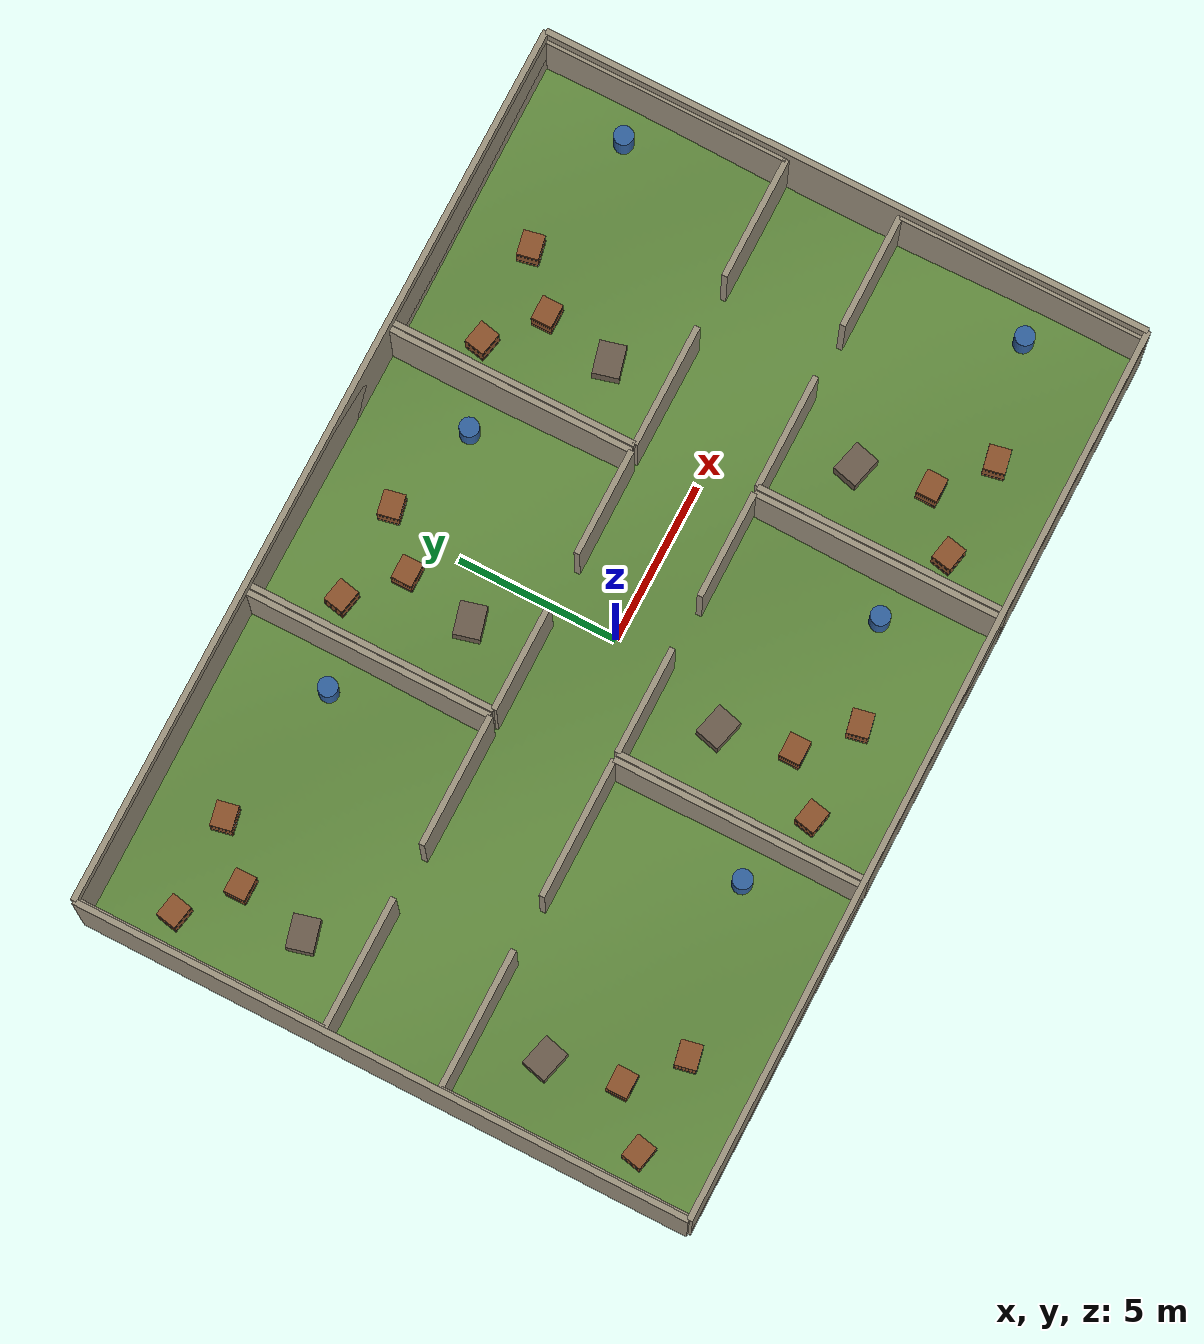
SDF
<?xml version='1.0' encoding='utf-8'?>
<sdf version="1.7">
  <world name="terrain_M3">
    <gravity>0 0 -9.8</gravity>
    <plugin name="gazebo_ros_state" filename="libgazebo_ros_state.so">
      <ros>
        <namespace>/gazebo</namespace>
      </ros>
    </plugin>
    <physics name="ode_physics" type="ode">
      <max_step_size>0.001</max_step_size>
      <real_time_factor>1</real_time_factor>
      <real_time_update_rate>1000</real_time_update_rate>
      <ode>
        <solver>
          <type>quick</type>
          <iters>150</iters>
          <sor>1.3</sor>
        </solver>
        <constraints>
          <cfm>0</cfm>
          <erp>0.2</erp>
          <contact_max_correcting_vel>0.2</contact_max_correcting_vel>
          <contact_surface_layer>0.001</contact_surface_layer>
        </constraints>
      </ode>
    </physics>
    <light name="sun" type="directional">
      <pose>0 0 42 0 0 0</pose>
      <diffuse>0.92 0.91 0.88 1</diffuse>
      <specular>0.18 0.18 0.16 1</specular>
      <direction>-0.35 -0.28 -0.9</direction>
      <cast_shadows>true</cast_shadows>
    </light>
    <light name="fill" type="point">
      <pose>0 0 6 0 0 0</pose>
      <diffuse>0.35 0.36 0.34 1</diffuse>
      <specular>0.02 0.02 0.02 1</specular>
      <cast_shadows>false</cast_shadows>
      <attenuation>
        <range>80</range>
        <constant>0.5</constant>
        <linear>0.02</linear>
      </attenuation>
    </light>
    <scene>
      <ambient>0.52 0.56 0.48 1</ambient>
      <background>0.58 0.76 0.92 1</background>
    </scene>
    <gui fullscreen="false">
      <camera name="user_camera">
        <pose>19.6 -17.1 23.8 0 0.65 2.2</pose>
        <view_controller>orbit</view_controller>
      </camera>
    </gui>
    <model name="terrain_M3_structure">
      <static>true</static>
      <link name="structure">
        <collision name="terrain_surface_collision">
          <pose>0 0 0 0 0 0</pose>
          <geometry>
            <mesh>
              <uri>3DModel/unseen/M3/terrain_surface.stl</uri>
            </mesh>
          </geometry>
          <max_contacts>40</max_contacts>
          <surface>
            <friction>
              <ode>
                <mu>8</mu>
                <mu2>8</mu2>
              </ode>
            </friction>
            <contact>
              <ode>
                <kp>1e7</kp>
                <kd>1000</kd>
                <max_vel>0.1</max_vel>
                <min_depth>0.001</min_depth>
              </ode>
            </contact>
          </surface>
        </collision>
        <visual name="terrain_surface_visual">
          <pose>0 0 0 0 0 0</pose>
          <geometry>
            <mesh>
              <uri>3DModel/unseen/M3/terrain_surface.stl</uri>
            </mesh>
          </geometry>
          <material>
            <ambient>0.38 0.54 0.24 1</ambient>
            <diffuse>0.38 0.54 0.24 1</diffuse>
          </material>
        </visual>
        <collision name="outer_south_wall_0_collision">
          <pose>0 -9.5 1.85 0 0 0</pose>
          <geometry>
            <box>
              <size>28 0.18 3.9</size>
            </box>
          </geometry>
          <max_contacts>40</max_contacts>
          <surface>
            <friction>
              <ode>
                <mu>2</mu>
                <mu2>2</mu2>
              </ode>
            </friction>
            <contact>
              <ode>
                <kp>1e7</kp>
                <kd>1000</kd>
                <max_vel>0.1</max_vel>
                <min_depth>0.001</min_depth>
              </ode>
            </contact>
          </surface>
        </collision>
        <visual name="outer_south_wall_0_visual">
          <pose>0 -9.5 1.85 0 0 0</pose>
          <geometry>
            <box>
              <size>28 0.18 3.9</size>
            </box>
          </geometry>
          <material>
            <ambient>0.62 0.58 0.50 1</ambient>
            <diffuse>0.62 0.58 0.50 1</diffuse>
          </material>
        </visual>
        <collision name="outer_north_wall_0_collision">
          <pose>0 9.5 1.85 0 0 0</pose>
          <geometry>
            <box>
              <size>28 0.18 3.9</size>
            </box>
          </geometry>
          <max_contacts>40</max_contacts>
          <surface>
            <friction>
              <ode>
                <mu>2</mu>
                <mu2>2</mu2>
              </ode>
            </friction>
            <contact>
              <ode>
                <kp>1e7</kp>
                <kd>1000</kd>
                <max_vel>0.1</max_vel>
                <min_depth>0.001</min_depth>
              </ode>
            </contact>
          </surface>
        </collision>
        <visual name="outer_north_wall_0_visual">
          <pose>0 9.5 1.85 0 0 0</pose>
          <geometry>
            <box>
              <size>28 0.18 3.9</size>
            </box>
          </geometry>
          <material>
            <ambient>0.62 0.58 0.50 1</ambient>
            <diffuse>0.62 0.58 0.50 1</diffuse>
          </material>
        </visual>
        <collision name="outer_west_wall_0_collision">
          <pose>-14 0 1.85 0 0 1.57079633</pose>
          <geometry>
            <box>
              <size>19 0.18 3.9</size>
            </box>
          </geometry>
          <max_contacts>40</max_contacts>
          <surface>
            <friction>
              <ode>
                <mu>2</mu>
                <mu2>2</mu2>
              </ode>
            </friction>
            <contact>
              <ode>
                <kp>1e7</kp>
                <kd>1000</kd>
                <max_vel>0.1</max_vel>
                <min_depth>0.001</min_depth>
              </ode>
            </contact>
          </surface>
        </collision>
        <visual name="outer_west_wall_0_visual">
          <pose>-14 0 1.85 0 0 1.57079633</pose>
          <geometry>
            <box>
              <size>19 0.18 3.9</size>
            </box>
          </geometry>
          <material>
            <ambient>0.62 0.58 0.50 1</ambient>
            <diffuse>0.62 0.58 0.50 1</diffuse>
          </material>
        </visual>
        <collision name="outer_east_wall_0_collision">
          <pose>14 0 1.85 0 0 1.57079633</pose>
          <geometry>
            <box>
              <size>19 0.18 3.9</size>
            </box>
          </geometry>
          <max_contacts>40</max_contacts>
          <surface>
            <friction>
              <ode>
                <mu>2</mu>
                <mu2>2</mu2>
              </ode>
            </friction>
            <contact>
              <ode>
                <kp>1e7</kp>
                <kd>1000</kd>
                <max_vel>0.1</max_vel>
                <min_depth>0.001</min_depth>
              </ode>
            </contact>
          </surface>
        </collision>
        <visual name="outer_east_wall_0_visual">
          <pose>14 0 1.85 0 0 1.57079633</pose>
          <geometry>
            <box>
              <size>19 0.18 3.9</size>
            </box>
          </geometry>
          <material>
            <ambient>0.62 0.58 0.50 1</ambient>
            <diffuse>0.62 0.58 0.50 1</diffuse>
          </material>
        </visual>
        <collision name="terrain_room_1_0_south_wall_0_collision">
          <pose>-11.8625 1.8 1.745 0 0 0</pose>
          <geometry>
            <box>
              <size>4.075 0.18 3.15</size>
            </box>
          </geometry>
          <max_contacts>40</max_contacts>
          <surface>
            <friction>
              <ode>
                <mu>2</mu>
                <mu2>2</mu2>
              </ode>
            </friction>
            <contact>
              <ode>
                <kp>1e7</kp>
                <kd>1000</kd>
                <max_vel>0.1</max_vel>
                <min_depth>0.001</min_depth>
              </ode>
            </contact>
          </surface>
        </collision>
        <visual name="terrain_room_1_0_south_wall_0_visual">
          <pose>-11.8625 1.8 1.745 0 0 0</pose>
          <geometry>
            <box>
              <size>4.075 0.18 3.15</size>
            </box>
          </geometry>
          <material>
            <ambient>0.62 0.58 0.50 1</ambient>
            <diffuse>0.62 0.58 0.50 1</diffuse>
          </material>
        </visual>
        <collision name="terrain_room_1_0_south_wall_1_collision">
          <pose>-6.1375 1.8 1.745 0 0 0</pose>
          <geometry>
            <box>
              <size>4.075 0.18 3.15</size>
            </box>
          </geometry>
          <max_contacts>40</max_contacts>
          <surface>
            <friction>
              <ode>
                <mu>2</mu>
                <mu2>2</mu2>
              </ode>
            </friction>
            <contact>
              <ode>
                <kp>1e7</kp>
                <kd>1000</kd>
                <max_vel>0.1</max_vel>
                <min_depth>0.001</min_depth>
              </ode>
            </contact>
          </surface>
        </collision>
        <visual name="terrain_room_1_0_south_wall_1_visual">
          <pose>-6.1375 1.8 1.745 0 0 0</pose>
          <geometry>
            <box>
              <size>4.075 0.18 3.15</size>
            </box>
          </geometry>
          <material>
            <ambient>0.62 0.58 0.50 1</ambient>
            <diffuse>0.62 0.58 0.50 1</diffuse>
          </material>
        </visual>
        <collision name="terrain_room_1_0_north_wall_0_collision">
          <pose>-9 9.5 1.745 0 0 0</pose>
          <geometry>
            <box>
              <size>9.8 0.18 3.15</size>
            </box>
          </geometry>
          <max_contacts>40</max_contacts>
          <surface>
            <friction>
              <ode>
                <mu>2</mu>
                <mu2>2</mu2>
              </ode>
            </friction>
            <contact>
              <ode>
                <kp>1e7</kp>
                <kd>1000</kd>
                <max_vel>0.1</max_vel>
                <min_depth>0.001</min_depth>
              </ode>
            </contact>
          </surface>
        </collision>
        <visual name="terrain_room_1_0_north_wall_0_visual">
          <pose>-9 9.5 1.745 0 0 0</pose>
          <geometry>
            <box>
              <size>9.8 0.18 3.15</size>
            </box>
          </geometry>
          <material>
            <ambient>0.62 0.58 0.50 1</ambient>
            <diffuse>0.62 0.58 0.50 1</diffuse>
          </material>
        </visual>
        <collision name="terrain_room_1_0_west_wall_0_collision">
          <pose>-13.9 5.65 1.745 0 0 1.57079633</pose>
          <geometry>
            <box>
              <size>7.7 0.18 3.15</size>
            </box>
          </geometry>
          <max_contacts>40</max_contacts>
          <surface>
            <friction>
              <ode>
                <mu>2</mu>
                <mu2>2</mu2>
              </ode>
            </friction>
            <contact>
              <ode>
                <kp>1e7</kp>
                <kd>1000</kd>
                <max_vel>0.1</max_vel>
                <min_depth>0.001</min_depth>
              </ode>
            </contact>
          </surface>
        </collision>
        <visual name="terrain_room_1_0_west_wall_0_visual">
          <pose>-13.9 5.65 1.745 0 0 1.57079633</pose>
          <geometry>
            <box>
              <size>7.7 0.18 3.15</size>
            </box>
          </geometry>
          <material>
            <ambient>0.62 0.58 0.50 1</ambient>
            <diffuse>0.62 0.58 0.50 1</diffuse>
          </material>
        </visual>
        <collision name="terrain_room_1_0_east_wall_0_collision">
          <pose>-4.1 5.65 1.745 0 0 1.57079633</pose>
          <geometry>
            <box>
              <size>7.7 0.18 3.15</size>
            </box>
          </geometry>
          <max_contacts>40</max_contacts>
          <surface>
            <friction>
              <ode>
                <mu>2</mu>
                <mu2>2</mu2>
              </ode>
            </friction>
            <contact>
              <ode>
                <kp>1e7</kp>
                <kd>1000</kd>
                <max_vel>0.1</max_vel>
                <min_depth>0.001</min_depth>
              </ode>
            </contact>
          </surface>
        </collision>
        <visual name="terrain_room_1_0_east_wall_0_visual">
          <pose>-4.1 5.65 1.745 0 0 1.57079633</pose>
          <geometry>
            <box>
              <size>7.7 0.18 3.15</size>
            </box>
          </geometry>
          <material>
            <ambient>0.62 0.58 0.50 1</ambient>
            <diffuse>0.62 0.58 0.50 1</diffuse>
          </material>
        </visual>
        <collision name="room_crate_1_0_0_prop_collision">
          <pose>-12.7 7.3 0.68582319 0 0 -0.2</pose>
          <geometry>
            <box>
              <size>0.75 0.65 0.8</size>
            </box>
          </geometry>
          <max_contacts>40</max_contacts>
          <surface>
            <friction>
              <ode>
                <mu>2</mu>
                <mu2>2</mu2>
              </ode>
            </friction>
            <contact>
              <ode>
                <kp>1e7</kp>
                <kd>1000</kd>
                <max_vel>0.1</max_vel>
                <min_depth>0.001</min_depth>
              </ode>
            </contact>
          </surface>
        </collision>
        <visual name="room_crate_1_0_0_prop_visual">
          <pose>-12.7 7.3 0.68582319 0 0 -0.2</pose>
          <geometry>
            <box>
              <size>0.75 0.65 0.8</size>
            </box>
          </geometry>
          <material>
            <ambient>0.55 0.32 0.17 1</ambient>
            <diffuse>0.55 0.32 0.17 1</diffuse>
          </material>
        </visual>
        <visual name="room_crate_1_0_0_strap_-1_visual">
          <pose>-12.7 7.3 0.44582319 0 0 -0.2</pose>
          <geometry>
            <box>
              <size>0.762 0.662 0.035</size>
            </box>
          </geometry>
          <material>
            <ambient>0.15 0.18 0.21 1</ambient>
            <diffuse>0.15 0.18 0.21 1</diffuse>
          </material>
        </visual>
        <visual name="room_crate_1_0_0_strap_1_visual">
          <pose>-12.7 7.3 0.92582319 0 0 -0.2</pose>
          <geometry>
            <box>
              <size>0.762 0.662 0.035</size>
            </box>
          </geometry>
          <material>
            <ambient>0.15 0.18 0.21 1</ambient>
            <diffuse>0.15 0.18 0.21 1</diffuse>
          </material>
        </visual>
        <collision name="room_crate_1_0_1_prop_collision">
          <pose>-11.2 6 0.759078075 0 0 0</pose>
          <geometry>
            <box>
              <size>0.75 0.65 0.8</size>
            </box>
          </geometry>
          <max_contacts>40</max_contacts>
          <surface>
            <friction>
              <ode>
                <mu>2</mu>
                <mu2>2</mu2>
              </ode>
            </friction>
            <contact>
              <ode>
                <kp>1e7</kp>
                <kd>1000</kd>
                <max_vel>0.1</max_vel>
                <min_depth>0.001</min_depth>
              </ode>
            </contact>
          </surface>
        </collision>
        <visual name="room_crate_1_0_1_prop_visual">
          <pose>-11.2 6 0.759078075 0 0 0</pose>
          <geometry>
            <box>
              <size>0.75 0.65 0.8</size>
            </box>
          </geometry>
          <material>
            <ambient>0.55 0.32 0.17 1</ambient>
            <diffuse>0.55 0.32 0.17 1</diffuse>
          </material>
        </visual>
        <visual name="room_crate_1_0_1_strap_-1_visual">
          <pose>-11.2 6 0.519078075 0 0 0</pose>
          <geometry>
            <box>
              <size>0.762 0.662 0.035</size>
            </box>
          </geometry>
          <material>
            <ambient>0.15 0.18 0.21 1</ambient>
            <diffuse>0.15 0.18 0.21 1</diffuse>
          </material>
        </visual>
        <visual name="room_crate_1_0_1_strap_1_visual">
          <pose>-11.2 6 0.999078075 0 0 0</pose>
          <geometry>
            <box>
              <size>0.762 0.662 0.035</size>
            </box>
          </geometry>
          <material>
            <ambient>0.15 0.18 0.21 1</ambient>
            <diffuse>0.15 0.18 0.21 1</diffuse>
          </material>
        </visual>
        <collision name="room_crate_1_0_2_prop_collision">
          <pose>-9.7 7.3 0.836859624 0 0 0.2</pose>
          <geometry>
            <box>
              <size>0.75 0.65 0.8</size>
            </box>
          </geometry>
          <max_contacts>40</max_contacts>
          <surface>
            <friction>
              <ode>
                <mu>2</mu>
                <mu2>2</mu2>
              </ode>
            </friction>
            <contact>
              <ode>
                <kp>1e7</kp>
                <kd>1000</kd>
                <max_vel>0.1</max_vel>
                <min_depth>0.001</min_depth>
              </ode>
            </contact>
          </surface>
        </collision>
        <visual name="room_crate_1_0_2_prop_visual">
          <pose>-9.7 7.3 0.836859624 0 0 0.2</pose>
          <geometry>
            <box>
              <size>0.75 0.65 0.8</size>
            </box>
          </geometry>
          <material>
            <ambient>0.55 0.32 0.17 1</ambient>
            <diffuse>0.55 0.32 0.17 1</diffuse>
          </material>
        </visual>
        <visual name="room_crate_1_0_2_strap_-1_visual">
          <pose>-9.7 7.3 0.596859624 0 0 0.2</pose>
          <geometry>
            <box>
              <size>0.762 0.662 0.035</size>
            </box>
          </geometry>
          <material>
            <ambient>0.15 0.18 0.21 1</ambient>
            <diffuse>0.15 0.18 0.21 1</diffuse>
          </material>
        </visual>
        <visual name="room_crate_1_0_2_strap_1_visual">
          <pose>-9.7 7.3 1.07685962 0 0 0.2</pose>
          <geometry>
            <box>
              <size>0.762 0.662 0.035</size>
            </box>
          </geometry>
          <material>
            <ambient>0.15 0.18 0.21 1</ambient>
            <diffuse>0.15 0.18 0.21 1</diffuse>
          </material>
        </visual>
        <collision name="room_barrel_prop_1_0_collision">
          <pose>-5.2 6.4 1.21632334 0 0 0</pose>
          <geometry>
            <cylinder>
              <radius>0.3</radius>
              <length>0.9</length>
            </cylinder>
          </geometry>
          <max_contacts>40</max_contacts>
          <surface>
            <friction>
              <ode>
                <mu>2</mu>
                <mu2>2</mu2>
              </ode>
            </friction>
            <contact>
              <ode>
                <kp>1e7</kp>
                <kd>1000</kd>
                <max_vel>0.1</max_vel>
                <min_depth>0.001</min_depth>
              </ode>
            </contact>
          </surface>
        </collision>
        <visual name="room_barrel_prop_1_0_visual">
          <pose>-5.2 6.4 1.21632334 0 0 0</pose>
          <geometry>
            <cylinder>
              <radius>0.3</radius>
              <length>0.9</length>
            </cylinder>
          </geometry>
          <material>
            <ambient>0.19 0.38 0.62 1</ambient>
            <diffuse>0.19 0.38 0.62 1</diffuse>
          </material>
        </visual>
        <collision name="room_block_obstacle_1_0_collision">
          <pose>-11.6 3.8 0.799242574 0 0 0.25</pose>
          <geometry>
            <box>
              <size>1 0.8 0.6</size>
            </box>
          </geometry>
          <max_contacts>40</max_contacts>
          <surface>
            <friction>
              <ode>
                <mu>2</mu>
                <mu2>2</mu2>
              </ode>
            </friction>
            <contact>
              <ode>
                <kp>1e7</kp>
                <kd>1000</kd>
                <max_vel>0.1</max_vel>
                <min_depth>0.001</min_depth>
              </ode>
            </contact>
          </surface>
        </collision>
        <visual name="room_block_obstacle_1_0_visual">
          <pose>-11.6 3.8 0.799242574 0 0 0.25</pose>
          <geometry>
            <box>
              <size>1 0.8 0.6</size>
            </box>
          </geometry>
          <material>
            <ambient>0.42 0.36 0.30 1</ambient>
            <diffuse>0.42 0.36 0.30 1</diffuse>
          </material>
        </visual>
        <collision name="terrain_room_1_1_south_wall_0_collision">
          <pose>-2.2375 1.8 1.745 0 0 0</pose>
          <geometry>
            <box>
              <size>3.325 0.18 3.15</size>
            </box>
          </geometry>
          <max_contacts>40</max_contacts>
          <surface>
            <friction>
              <ode>
                <mu>2</mu>
                <mu2>2</mu2>
              </ode>
            </friction>
            <contact>
              <ode>
                <kp>1e7</kp>
                <kd>1000</kd>
                <max_vel>0.1</max_vel>
                <min_depth>0.001</min_depth>
              </ode>
            </contact>
          </surface>
        </collision>
        <visual name="terrain_room_1_1_south_wall_0_visual">
          <pose>-2.2375 1.8 1.745 0 0 0</pose>
          <geometry>
            <box>
              <size>3.325 0.18 3.15</size>
            </box>
          </geometry>
          <material>
            <ambient>0.62 0.58 0.50 1</ambient>
            <diffuse>0.62 0.58 0.50 1</diffuse>
          </material>
        </visual>
        <collision name="terrain_room_1_1_south_wall_1_collision">
          <pose>2.7375 1.8 1.745 0 0 0</pose>
          <geometry>
            <box>
              <size>3.325 0.18 3.15</size>
            </box>
          </geometry>
          <max_contacts>40</max_contacts>
          <surface>
            <friction>
              <ode>
                <mu>2</mu>
                <mu2>2</mu2>
              </ode>
            </friction>
            <contact>
              <ode>
                <kp>1e7</kp>
                <kd>1000</kd>
                <max_vel>0.1</max_vel>
                <min_depth>0.001</min_depth>
              </ode>
            </contact>
          </surface>
        </collision>
        <visual name="terrain_room_1_1_south_wall_1_visual">
          <pose>2.7375 1.8 1.745 0 0 0</pose>
          <geometry>
            <box>
              <size>3.325 0.18 3.15</size>
            </box>
          </geometry>
          <material>
            <ambient>0.62 0.58 0.50 1</ambient>
            <diffuse>0.62 0.58 0.50 1</diffuse>
          </material>
        </visual>
        <collision name="terrain_room_1_1_north_wall_0_collision">
          <pose>0.25 9.5 1.745 0 0 0</pose>
          <geometry>
            <box>
              <size>8.3 0.18 3.15</size>
            </box>
          </geometry>
          <max_contacts>40</max_contacts>
          <surface>
            <friction>
              <ode>
                <mu>2</mu>
                <mu2>2</mu2>
              </ode>
            </friction>
            <contact>
              <ode>
                <kp>1e7</kp>
                <kd>1000</kd>
                <max_vel>0.1</max_vel>
                <min_depth>0.001</min_depth>
              </ode>
            </contact>
          </surface>
        </collision>
        <visual name="terrain_room_1_1_north_wall_0_visual">
          <pose>0.25 9.5 1.745 0 0 0</pose>
          <geometry>
            <box>
              <size>8.3 0.18 3.15</size>
            </box>
          </geometry>
          <material>
            <ambient>0.62 0.58 0.50 1</ambient>
            <diffuse>0.62 0.58 0.50 1</diffuse>
          </material>
        </visual>
        <collision name="terrain_room_1_1_west_wall_0_collision">
          <pose>-3.9 5.65 1.745 0 0 1.57079633</pose>
          <geometry>
            <box>
              <size>7.7 0.18 3.15</size>
            </box>
          </geometry>
          <max_contacts>40</max_contacts>
          <surface>
            <friction>
              <ode>
                <mu>2</mu>
                <mu2>2</mu2>
              </ode>
            </friction>
            <contact>
              <ode>
                <kp>1e7</kp>
                <kd>1000</kd>
                <max_vel>0.1</max_vel>
                <min_depth>0.001</min_depth>
              </ode>
            </contact>
          </surface>
        </collision>
        <visual name="terrain_room_1_1_west_wall_0_visual">
          <pose>-3.9 5.65 1.745 0 0 1.57079633</pose>
          <geometry>
            <box>
              <size>7.7 0.18 3.15</size>
            </box>
          </geometry>
          <material>
            <ambient>0.62 0.58 0.50 1</ambient>
            <diffuse>0.62 0.58 0.50 1</diffuse>
          </material>
        </visual>
        <collision name="terrain_room_1_1_east_wall_0_collision">
          <pose>4.4 5.65 1.745 0 0 1.57079633</pose>
          <geometry>
            <box>
              <size>7.7 0.18 3.15</size>
            </box>
          </geometry>
          <max_contacts>40</max_contacts>
          <surface>
            <friction>
              <ode>
                <mu>2</mu>
                <mu2>2</mu2>
              </ode>
            </friction>
            <contact>
              <ode>
                <kp>1e7</kp>
                <kd>1000</kd>
                <max_vel>0.1</max_vel>
                <min_depth>0.001</min_depth>
              </ode>
            </contact>
          </surface>
        </collision>
        <visual name="terrain_room_1_1_east_wall_0_visual">
          <pose>4.4 5.65 1.745 0 0 1.57079633</pose>
          <geometry>
            <box>
              <size>7.7 0.18 3.15</size>
            </box>
          </geometry>
          <material>
            <ambient>0.62 0.58 0.50 1</ambient>
            <diffuse>0.62 0.58 0.50 1</diffuse>
          </material>
        </visual>
        <collision name="room_crate_1_1_0_prop_collision">
          <pose>-2.7 7.3 1.18072693 0 0 -0.2</pose>
          <geometry>
            <box>
              <size>0.75 0.65 0.8</size>
            </box>
          </geometry>
          <max_contacts>40</max_contacts>
          <surface>
            <friction>
              <ode>
                <mu>2</mu>
                <mu2>2</mu2>
              </ode>
            </friction>
            <contact>
              <ode>
                <kp>1e7</kp>
                <kd>1000</kd>
                <max_vel>0.1</max_vel>
                <min_depth>0.001</min_depth>
              </ode>
            </contact>
          </surface>
        </collision>
        <visual name="room_crate_1_1_0_prop_visual">
          <pose>-2.7 7.3 1.18072693 0 0 -0.2</pose>
          <geometry>
            <box>
              <size>0.75 0.65 0.8</size>
            </box>
          </geometry>
          <material>
            <ambient>0.55 0.32 0.17 1</ambient>
            <diffuse>0.55 0.32 0.17 1</diffuse>
          </material>
        </visual>
        <visual name="room_crate_1_1_0_strap_-1_visual">
          <pose>-2.7 7.3 0.940726934 0 0 -0.2</pose>
          <geometry>
            <box>
              <size>0.762 0.662 0.035</size>
            </box>
          </geometry>
          <material>
            <ambient>0.15 0.18 0.21 1</ambient>
            <diffuse>0.15 0.18 0.21 1</diffuse>
          </material>
        </visual>
        <visual name="room_crate_1_1_0_strap_1_visual">
          <pose>-2.7 7.3 1.42072693 0 0 -0.2</pose>
          <geometry>
            <box>
              <size>0.762 0.662 0.035</size>
            </box>
          </geometry>
          <material>
            <ambient>0.15 0.18 0.21 1</ambient>
            <diffuse>0.15 0.18 0.21 1</diffuse>
          </material>
        </visual>
        <collision name="room_crate_1_1_1_prop_collision">
          <pose>-1.2 6 1.09067439 0 0 0</pose>
          <geometry>
            <box>
              <size>0.75 0.65 0.8</size>
            </box>
          </geometry>
          <max_contacts>40</max_contacts>
          <surface>
            <friction>
              <ode>
                <mu>2</mu>
                <mu2>2</mu2>
              </ode>
            </friction>
            <contact>
              <ode>
                <kp>1e7</kp>
                <kd>1000</kd>
                <max_vel>0.1</max_vel>
                <min_depth>0.001</min_depth>
              </ode>
            </contact>
          </surface>
        </collision>
        <visual name="room_crate_1_1_1_prop_visual">
          <pose>-1.2 6 1.09067439 0 0 0</pose>
          <geometry>
            <box>
              <size>0.75 0.65 0.8</size>
            </box>
          </geometry>
          <material>
            <ambient>0.55 0.32 0.17 1</ambient>
            <diffuse>0.55 0.32 0.17 1</diffuse>
          </material>
        </visual>
        <visual name="room_crate_1_1_1_strap_-1_visual">
          <pose>-1.2 6 0.850674393 0 0 0</pose>
          <geometry>
            <box>
              <size>0.762 0.662 0.035</size>
            </box>
          </geometry>
          <material>
            <ambient>0.15 0.18 0.21 1</ambient>
            <diffuse>0.15 0.18 0.21 1</diffuse>
          </material>
        </visual>
        <visual name="room_crate_1_1_1_strap_1_visual">
          <pose>-1.2 6 1.33067439 0 0 0</pose>
          <geometry>
            <box>
              <size>0.762 0.662 0.035</size>
            </box>
          </geometry>
          <material>
            <ambient>0.15 0.18 0.21 1</ambient>
            <diffuse>0.15 0.18 0.21 1</diffuse>
          </material>
        </visual>
        <collision name="room_crate_1_1_2_prop_collision">
          <pose>0.3 7.3 0.998318562 0 0 0.2</pose>
          <geometry>
            <box>
              <size>0.75 0.65 0.8</size>
            </box>
          </geometry>
          <max_contacts>40</max_contacts>
          <surface>
            <friction>
              <ode>
                <mu>2</mu>
                <mu2>2</mu2>
              </ode>
            </friction>
            <contact>
              <ode>
                <kp>1e7</kp>
                <kd>1000</kd>
                <max_vel>0.1</max_vel>
                <min_depth>0.001</min_depth>
              </ode>
            </contact>
          </surface>
        </collision>
        <visual name="room_crate_1_1_2_prop_visual">
          <pose>0.3 7.3 0.998318562 0 0 0.2</pose>
          <geometry>
            <box>
              <size>0.75 0.65 0.8</size>
            </box>
          </geometry>
          <material>
            <ambient>0.55 0.32 0.17 1</ambient>
            <diffuse>0.55 0.32 0.17 1</diffuse>
          </material>
        </visual>
        <visual name="room_crate_1_1_2_strap_-1_visual">
          <pose>0.3 7.3 0.758318562 0 0 0.2</pose>
          <geometry>
            <box>
              <size>0.762 0.662 0.035</size>
            </box>
          </geometry>
          <material>
            <ambient>0.15 0.18 0.21 1</ambient>
            <diffuse>0.15 0.18 0.21 1</diffuse>
          </material>
        </visual>
        <visual name="room_crate_1_1_2_strap_1_visual">
          <pose>0.3 7.3 1.23831856 0 0 0.2</pose>
          <geometry>
            <box>
              <size>0.762 0.662 0.035</size>
            </box>
          </geometry>
          <material>
            <ambient>0.15 0.18 0.21 1</ambient>
            <diffuse>0.15 0.18 0.21 1</diffuse>
          </material>
        </visual>
        <collision name="room_barrel_prop_1_1_collision">
          <pose>3.3 6.4 0.906111311 0 0 0</pose>
          <geometry>
            <cylinder>
              <radius>0.3</radius>
              <length>0.9</length>
            </cylinder>
          </geometry>
          <max_contacts>40</max_contacts>
          <surface>
            <friction>
              <ode>
                <mu>2</mu>
                <mu2>2</mu2>
              </ode>
            </friction>
            <contact>
              <ode>
                <kp>1e7</kp>
                <kd>1000</kd>
                <max_vel>0.1</max_vel>
                <min_depth>0.001</min_depth>
              </ode>
            </contact>
          </surface>
        </collision>
        <visual name="room_barrel_prop_1_1_visual">
          <pose>3.3 6.4 0.906111311 0 0 0</pose>
          <geometry>
            <cylinder>
              <radius>0.3</radius>
              <length>0.9</length>
            </cylinder>
          </geometry>
          <material>
            <ambient>0.19 0.38 0.62 1</ambient>
            <diffuse>0.19 0.38 0.62 1</diffuse>
          </material>
        </visual>
        <collision name="room_block_obstacle_1_1_collision">
          <pose>-1.6 3.8 0.915588072 0 0 0.25</pose>
          <geometry>
            <box>
              <size>1 0.8 0.6</size>
            </box>
          </geometry>
          <max_contacts>40</max_contacts>
          <surface>
            <friction>
              <ode>
                <mu>2</mu>
                <mu2>2</mu2>
              </ode>
            </friction>
            <contact>
              <ode>
                <kp>1e7</kp>
                <kd>1000</kd>
                <max_vel>0.1</max_vel>
                <min_depth>0.001</min_depth>
              </ode>
            </contact>
          </surface>
        </collision>
        <visual name="room_block_obstacle_1_1_visual">
          <pose>-1.6 3.8 0.915588072 0 0 0.25</pose>
          <geometry>
            <box>
              <size>1 0.8 0.6</size>
            </box>
          </geometry>
          <material>
            <ambient>0.42 0.36 0.30 1</ambient>
            <diffuse>0.42 0.36 0.30 1</diffuse>
          </material>
        </visual>
        <collision name="terrain_room_1_2_south_wall_0_collision">
          <pose>6.5125 1.8 1.745 0 0 0</pose>
          <geometry>
            <box>
              <size>3.825 0.18 3.15</size>
            </box>
          </geometry>
          <max_contacts>40</max_contacts>
          <surface>
            <friction>
              <ode>
                <mu>2</mu>
                <mu2>2</mu2>
              </ode>
            </friction>
            <contact>
              <ode>
                <kp>1e7</kp>
                <kd>1000</kd>
                <max_vel>0.1</max_vel>
                <min_depth>0.001</min_depth>
              </ode>
            </contact>
          </surface>
        </collision>
        <visual name="terrain_room_1_2_south_wall_0_visual">
          <pose>6.5125 1.8 1.745 0 0 0</pose>
          <geometry>
            <box>
              <size>3.825 0.18 3.15</size>
            </box>
          </geometry>
          <material>
            <ambient>0.62 0.58 0.50 1</ambient>
            <diffuse>0.62 0.58 0.50 1</diffuse>
          </material>
        </visual>
        <collision name="terrain_room_1_2_south_wall_1_collision">
          <pose>11.9875 1.8 1.745 0 0 0</pose>
          <geometry>
            <box>
              <size>3.825 0.18 3.15</size>
            </box>
          </geometry>
          <max_contacts>40</max_contacts>
          <surface>
            <friction>
              <ode>
                <mu>2</mu>
                <mu2>2</mu2>
              </ode>
            </friction>
            <contact>
              <ode>
                <kp>1e7</kp>
                <kd>1000</kd>
                <max_vel>0.1</max_vel>
                <min_depth>0.001</min_depth>
              </ode>
            </contact>
          </surface>
        </collision>
        <visual name="terrain_room_1_2_south_wall_1_visual">
          <pose>11.9875 1.8 1.745 0 0 0</pose>
          <geometry>
            <box>
              <size>3.825 0.18 3.15</size>
            </box>
          </geometry>
          <material>
            <ambient>0.62 0.58 0.50 1</ambient>
            <diffuse>0.62 0.58 0.50 1</diffuse>
          </material>
        </visual>
        <collision name="terrain_room_1_2_north_wall_0_collision">
          <pose>9.25 9.5 1.745 0 0 0</pose>
          <geometry>
            <box>
              <size>9.3 0.18 3.15</size>
            </box>
          </geometry>
          <max_contacts>40</max_contacts>
          <surface>
            <friction>
              <ode>
                <mu>2</mu>
                <mu2>2</mu2>
              </ode>
            </friction>
            <contact>
              <ode>
                <kp>1e7</kp>
                <kd>1000</kd>
                <max_vel>0.1</max_vel>
                <min_depth>0.001</min_depth>
              </ode>
            </contact>
          </surface>
        </collision>
        <visual name="terrain_room_1_2_north_wall_0_visual">
          <pose>9.25 9.5 1.745 0 0 0</pose>
          <geometry>
            <box>
              <size>9.3 0.18 3.15</size>
            </box>
          </geometry>
          <material>
            <ambient>0.62 0.58 0.50 1</ambient>
            <diffuse>0.62 0.58 0.50 1</diffuse>
          </material>
        </visual>
        <collision name="terrain_room_1_2_west_wall_0_collision">
          <pose>4.6 5.65 1.745 0 0 1.57079633</pose>
          <geometry>
            <box>
              <size>7.7 0.18 3.15</size>
            </box>
          </geometry>
          <max_contacts>40</max_contacts>
          <surface>
            <friction>
              <ode>
                <mu>2</mu>
                <mu2>2</mu2>
              </ode>
            </friction>
            <contact>
              <ode>
                <kp>1e7</kp>
                <kd>1000</kd>
                <max_vel>0.1</max_vel>
                <min_depth>0.001</min_depth>
              </ode>
            </contact>
          </surface>
        </collision>
        <visual name="terrain_room_1_2_west_wall_0_visual">
          <pose>4.6 5.65 1.745 0 0 1.57079633</pose>
          <geometry>
            <box>
              <size>7.7 0.18 3.15</size>
            </box>
          </geometry>
          <material>
            <ambient>0.62 0.58 0.50 1</ambient>
            <diffuse>0.62 0.58 0.50 1</diffuse>
          </material>
        </visual>
        <collision name="terrain_room_1_2_east_wall_0_collision">
          <pose>13.9 5.65 1.745 0 0 1.57079633</pose>
          <geometry>
            <box>
              <size>7.7 0.18 3.15</size>
            </box>
          </geometry>
          <max_contacts>40</max_contacts>
          <surface>
            <friction>
              <ode>
                <mu>2</mu>
                <mu2>2</mu2>
              </ode>
            </friction>
            <contact>
              <ode>
                <kp>1e7</kp>
                <kd>1000</kd>
                <max_vel>0.1</max_vel>
                <min_depth>0.001</min_depth>
              </ode>
            </contact>
          </surface>
        </collision>
        <visual name="terrain_room_1_2_east_wall_0_visual">
          <pose>13.9 5.65 1.745 0 0 1.57079633</pose>
          <geometry>
            <box>
              <size>7.7 0.18 3.15</size>
            </box>
          </geometry>
          <material>
            <ambient>0.62 0.58 0.50 1</ambient>
            <diffuse>0.62 0.58 0.50 1</diffuse>
          </material>
        </visual>
        <collision name="room_crate_1_2_0_prop_collision">
          <pose>5.8 7.3 0.887955858 0 0 -0.2</pose>
          <geometry>
            <box>
              <size>0.75 0.65 0.8</size>
            </box>
          </geometry>
          <max_contacts>40</max_contacts>
          <surface>
            <friction>
              <ode>
                <mu>2</mu>
                <mu2>2</mu2>
              </ode>
            </friction>
            <contact>
              <ode>
                <kp>1e7</kp>
                <kd>1000</kd>
                <max_vel>0.1</max_vel>
                <min_depth>0.001</min_depth>
              </ode>
            </contact>
          </surface>
        </collision>
        <visual name="room_crate_1_2_0_prop_visual">
          <pose>5.8 7.3 0.887955858 0 0 -0.2</pose>
          <geometry>
            <box>
              <size>0.75 0.65 0.8</size>
            </box>
          </geometry>
          <material>
            <ambient>0.55 0.32 0.17 1</ambient>
            <diffuse>0.55 0.32 0.17 1</diffuse>
          </material>
        </visual>
        <visual name="room_crate_1_2_0_strap_-1_visual">
          <pose>5.8 7.3 0.647955858 0 0 -0.2</pose>
          <geometry>
            <box>
              <size>0.762 0.662 0.035</size>
            </box>
          </geometry>
          <material>
            <ambient>0.15 0.18 0.21 1</ambient>
            <diffuse>0.15 0.18 0.21 1</diffuse>
          </material>
        </visual>
        <visual name="room_crate_1_2_0_strap_1_visual">
          <pose>5.8 7.3 1.12795586 0 0 -0.2</pose>
          <geometry>
            <box>
              <size>0.762 0.662 0.035</size>
            </box>
          </geometry>
          <material>
            <ambient>0.15 0.18 0.21 1</ambient>
            <diffuse>0.15 0.18 0.21 1</diffuse>
          </material>
        </visual>
        <collision name="room_crate_1_2_1_prop_collision">
          <pose>7.3 6 1.0053489 0 0 0</pose>
          <geometry>
            <box>
              <size>0.75 0.65 0.8</size>
            </box>
          </geometry>
          <max_contacts>40</max_contacts>
          <surface>
            <friction>
              <ode>
                <mu>2</mu>
                <mu2>2</mu2>
              </ode>
            </friction>
            <contact>
              <ode>
                <kp>1e7</kp>
                <kd>1000</kd>
                <max_vel>0.1</max_vel>
                <min_depth>0.001</min_depth>
              </ode>
            </contact>
          </surface>
        </collision>
        <visual name="room_crate_1_2_1_prop_visual">
          <pose>7.3 6 1.0053489 0 0 0</pose>
          <geometry>
            <box>
              <size>0.75 0.65 0.8</size>
            </box>
          </geometry>
          <material>
            <ambient>0.55 0.32 0.17 1</ambient>
            <diffuse>0.55 0.32 0.17 1</diffuse>
          </material>
        </visual>
        <visual name="room_crate_1_2_1_strap_-1_visual">
          <pose>7.3 6 0.765348897 0 0 0</pose>
          <geometry>
            <box>
              <size>0.762 0.662 0.035</size>
            </box>
          </geometry>
          <material>
            <ambient>0.15 0.18 0.21 1</ambient>
            <diffuse>0.15 0.18 0.21 1</diffuse>
          </material>
        </visual>
        <visual name="room_crate_1_2_1_strap_1_visual">
          <pose>7.3 6 1.2453489 0 0 0</pose>
          <geometry>
            <box>
              <size>0.762 0.662 0.035</size>
            </box>
          </geometry>
          <material>
            <ambient>0.15 0.18 0.21 1</ambient>
            <diffuse>0.15 0.18 0.21 1</diffuse>
          </material>
        </visual>
        <collision name="room_crate_1_2_2_prop_collision">
          <pose>8.8 7.3 1.12501347 0 0 0.2</pose>
          <geometry>
            <box>
              <size>0.75 0.65 0.8</size>
            </box>
          </geometry>
          <max_contacts>40</max_contacts>
          <surface>
            <friction>
              <ode>
                <mu>2</mu>
                <mu2>2</mu2>
              </ode>
            </friction>
            <contact>
              <ode>
                <kp>1e7</kp>
                <kd>1000</kd>
                <max_vel>0.1</max_vel>
                <min_depth>0.001</min_depth>
              </ode>
            </contact>
          </surface>
        </collision>
        <visual name="room_crate_1_2_2_prop_visual">
          <pose>8.8 7.3 1.12501347 0 0 0.2</pose>
          <geometry>
            <box>
              <size>0.75 0.65 0.8</size>
            </box>
          </geometry>
          <material>
            <ambient>0.55 0.32 0.17 1</ambient>
            <diffuse>0.55 0.32 0.17 1</diffuse>
          </material>
        </visual>
        <visual name="room_crate_1_2_2_strap_-1_visual">
          <pose>8.8 7.3 0.885013471 0 0 0.2</pose>
          <geometry>
            <box>
              <size>0.762 0.662 0.035</size>
            </box>
          </geometry>
          <material>
            <ambient>0.15 0.18 0.21 1</ambient>
            <diffuse>0.15 0.18 0.21 1</diffuse>
          </material>
        </visual>
        <visual name="room_crate_1_2_2_strap_1_visual">
          <pose>8.8 7.3 1.36501347 0 0 0.2</pose>
          <geometry>
            <box>
              <size>0.762 0.662 0.035</size>
            </box>
          </geometry>
          <material>
            <ambient>0.15 0.18 0.21 1</ambient>
            <diffuse>0.15 0.18 0.21 1</diffuse>
          </material>
        </visual>
        <collision name="room_barrel_prop_1_2_collision">
          <pose>12.8 6.4 1.39109316 0 0 0</pose>
          <geometry>
            <cylinder>
              <radius>0.3</radius>
              <length>0.9</length>
            </cylinder>
          </geometry>
          <max_contacts>40</max_contacts>
          <surface>
            <friction>
              <ode>
                <mu>2</mu>
                <mu2>2</mu2>
              </ode>
            </friction>
            <contact>
              <ode>
                <kp>1e7</kp>
                <kd>1000</kd>
                <max_vel>0.1</max_vel>
                <min_depth>0.001</min_depth>
              </ode>
            </contact>
          </surface>
        </collision>
        <visual name="room_barrel_prop_1_2_visual">
          <pose>12.8 6.4 1.39109316 0 0 0</pose>
          <geometry>
            <cylinder>
              <radius>0.3</radius>
              <length>0.9</length>
            </cylinder>
          </geometry>
          <material>
            <ambient>0.19 0.38 0.62 1</ambient>
            <diffuse>0.19 0.38 0.62 1</diffuse>
          </material>
        </visual>
        <collision name="room_block_obstacle_1_2_collision">
          <pose>6.9 3.8 0.972209387 0 0 0.25</pose>
          <geometry>
            <box>
              <size>1 0.8 0.6</size>
            </box>
          </geometry>
          <max_contacts>40</max_contacts>
          <surface>
            <friction>
              <ode>
                <mu>2</mu>
                <mu2>2</mu2>
              </ode>
            </friction>
            <contact>
              <ode>
                <kp>1e7</kp>
                <kd>1000</kd>
                <max_vel>0.1</max_vel>
                <min_depth>0.001</min_depth>
              </ode>
            </contact>
          </surface>
        </collision>
        <visual name="room_block_obstacle_1_2_visual">
          <pose>6.9 3.8 0.972209387 0 0 0.25</pose>
          <geometry>
            <box>
              <size>1 0.8 0.6</size>
            </box>
          </geometry>
          <material>
            <ambient>0.42 0.36 0.30 1</ambient>
            <diffuse>0.42 0.36 0.30 1</diffuse>
          </material>
        </visual>
        <collision name="terrain_room_-1_0_south_wall_0_collision">
          <pose>-8.75 -9.5 1.745 0 0 0</pose>
          <geometry>
            <box>
              <size>10.3 0.18 3.15</size>
            </box>
          </geometry>
          <max_contacts>40</max_contacts>
          <surface>
            <friction>
              <ode>
                <mu>2</mu>
                <mu2>2</mu2>
              </ode>
            </friction>
            <contact>
              <ode>
                <kp>1e7</kp>
                <kd>1000</kd>
                <max_vel>0.1</max_vel>
                <min_depth>0.001</min_depth>
              </ode>
            </contact>
          </surface>
        </collision>
        <visual name="terrain_room_-1_0_south_wall_0_visual">
          <pose>-8.75 -9.5 1.745 0 0 0</pose>
          <geometry>
            <box>
              <size>10.3 0.18 3.15</size>
            </box>
          </geometry>
          <material>
            <ambient>0.62 0.58 0.50 1</ambient>
            <diffuse>0.62 0.58 0.50 1</diffuse>
          </material>
        </visual>
        <collision name="terrain_room_-1_0_north_wall_0_collision">
          <pose>-11.7375 -1.8 1.745 0 0 0</pose>
          <geometry>
            <box>
              <size>4.325 0.18 3.15</size>
            </box>
          </geometry>
          <max_contacts>40</max_contacts>
          <surface>
            <friction>
              <ode>
                <mu>2</mu>
                <mu2>2</mu2>
              </ode>
            </friction>
            <contact>
              <ode>
                <kp>1e7</kp>
                <kd>1000</kd>
                <max_vel>0.1</max_vel>
                <min_depth>0.001</min_depth>
              </ode>
            </contact>
          </surface>
        </collision>
        <visual name="terrain_room_-1_0_north_wall_0_visual">
          <pose>-11.7375 -1.8 1.745 0 0 0</pose>
          <geometry>
            <box>
              <size>4.325 0.18 3.15</size>
            </box>
          </geometry>
          <material>
            <ambient>0.62 0.58 0.50 1</ambient>
            <diffuse>0.62 0.58 0.50 1</diffuse>
          </material>
        </visual>
        <collision name="terrain_room_-1_0_north_wall_1_collision">
          <pose>-5.7625 -1.8 1.745 0 0 0</pose>
          <geometry>
            <box>
              <size>4.325 0.18 3.15</size>
            </box>
          </geometry>
          <max_contacts>40</max_contacts>
          <surface>
            <friction>
              <ode>
                <mu>2</mu>
                <mu2>2</mu2>
              </ode>
            </friction>
            <contact>
              <ode>
                <kp>1e7</kp>
                <kd>1000</kd>
                <max_vel>0.1</max_vel>
                <min_depth>0.001</min_depth>
              </ode>
            </contact>
          </surface>
        </collision>
        <visual name="terrain_room_-1_0_north_wall_1_visual">
          <pose>-5.7625 -1.8 1.745 0 0 0</pose>
          <geometry>
            <box>
              <size>4.325 0.18 3.15</size>
            </box>
          </geometry>
          <material>
            <ambient>0.62 0.58 0.50 1</ambient>
            <diffuse>0.62 0.58 0.50 1</diffuse>
          </material>
        </visual>
        <collision name="terrain_room_-1_0_west_wall_0_collision">
          <pose>-13.9 -5.65 1.745 0 0 1.57079633</pose>
          <geometry>
            <box>
              <size>7.7 0.18 3.15</size>
            </box>
          </geometry>
          <max_contacts>40</max_contacts>
          <surface>
            <friction>
              <ode>
                <mu>2</mu>
                <mu2>2</mu2>
              </ode>
            </friction>
            <contact>
              <ode>
                <kp>1e7</kp>
                <kd>1000</kd>
                <max_vel>0.1</max_vel>
                <min_depth>0.001</min_depth>
              </ode>
            </contact>
          </surface>
        </collision>
        <visual name="terrain_room_-1_0_west_wall_0_visual">
          <pose>-13.9 -5.65 1.745 0 0 1.57079633</pose>
          <geometry>
            <box>
              <size>7.7 0.18 3.15</size>
            </box>
          </geometry>
          <material>
            <ambient>0.62 0.58 0.50 1</ambient>
            <diffuse>0.62 0.58 0.50 1</diffuse>
          </material>
        </visual>
        <collision name="terrain_room_-1_0_east_wall_0_collision">
          <pose>-3.6 -5.65 1.745 0 0 1.57079633</pose>
          <geometry>
            <box>
              <size>7.7 0.18 3.15</size>
            </box>
          </geometry>
          <max_contacts>40</max_contacts>
          <surface>
            <friction>
              <ode>
                <mu>2</mu>
                <mu2>2</mu2>
              </ode>
            </friction>
            <contact>
              <ode>
                <kp>1e7</kp>
                <kd>1000</kd>
                <max_vel>0.1</max_vel>
                <min_depth>0.001</min_depth>
              </ode>
            </contact>
          </surface>
        </collision>
        <visual name="terrain_room_-1_0_east_wall_0_visual">
          <pose>-3.6 -5.65 1.745 0 0 1.57079633</pose>
          <geometry>
            <box>
              <size>7.7 0.18 3.15</size>
            </box>
          </geometry>
          <material>
            <ambient>0.62 0.58 0.50 1</ambient>
            <diffuse>0.62 0.58 0.50 1</diffuse>
          </material>
        </visual>
        <collision name="room_crate_-1_0_0_prop_collision">
          <pose>-12.7 -7.3 0.68582319 0 0 -0.2</pose>
          <geometry>
            <box>
              <size>0.75 0.65 0.8</size>
            </box>
          </geometry>
          <max_contacts>40</max_contacts>
          <surface>
            <friction>
              <ode>
                <mu>2</mu>
                <mu2>2</mu2>
              </ode>
            </friction>
            <contact>
              <ode>
                <kp>1e7</kp>
                <kd>1000</kd>
                <max_vel>0.1</max_vel>
                <min_depth>0.001</min_depth>
              </ode>
            </contact>
          </surface>
        </collision>
        <visual name="room_crate_-1_0_0_prop_visual">
          <pose>-12.7 -7.3 0.68582319 0 0 -0.2</pose>
          <geometry>
            <box>
              <size>0.75 0.65 0.8</size>
            </box>
          </geometry>
          <material>
            <ambient>0.55 0.32 0.17 1</ambient>
            <diffuse>0.55 0.32 0.17 1</diffuse>
          </material>
        </visual>
        <visual name="room_crate_-1_0_0_strap_-1_visual">
          <pose>-12.7 -7.3 0.44582319 0 0 -0.2</pose>
          <geometry>
            <box>
              <size>0.762 0.662 0.035</size>
            </box>
          </geometry>
          <material>
            <ambient>0.15 0.18 0.21 1</ambient>
            <diffuse>0.15 0.18 0.21 1</diffuse>
          </material>
        </visual>
        <visual name="room_crate_-1_0_0_strap_1_visual">
          <pose>-12.7 -7.3 0.92582319 0 0 -0.2</pose>
          <geometry>
            <box>
              <size>0.762 0.662 0.035</size>
            </box>
          </geometry>
          <material>
            <ambient>0.15 0.18 0.21 1</ambient>
            <diffuse>0.15 0.18 0.21 1</diffuse>
          </material>
        </visual>
        <collision name="room_crate_-1_0_1_prop_collision">
          <pose>-11.2 -6 0.759078075 0 0 0</pose>
          <geometry>
            <box>
              <size>0.75 0.65 0.8</size>
            </box>
          </geometry>
          <max_contacts>40</max_contacts>
          <surface>
            <friction>
              <ode>
                <mu>2</mu>
                <mu2>2</mu2>
              </ode>
            </friction>
            <contact>
              <ode>
                <kp>1e7</kp>
                <kd>1000</kd>
                <max_vel>0.1</max_vel>
                <min_depth>0.001</min_depth>
              </ode>
            </contact>
          </surface>
        </collision>
        <visual name="room_crate_-1_0_1_prop_visual">
          <pose>-11.2 -6 0.759078075 0 0 0</pose>
          <geometry>
            <box>
              <size>0.75 0.65 0.8</size>
            </box>
          </geometry>
          <material>
            <ambient>0.55 0.32 0.17 1</ambient>
            <diffuse>0.55 0.32 0.17 1</diffuse>
          </material>
        </visual>
        <visual name="room_crate_-1_0_1_strap_-1_visual">
          <pose>-11.2 -6 0.519078075 0 0 0</pose>
          <geometry>
            <box>
              <size>0.762 0.662 0.035</size>
            </box>
          </geometry>
          <material>
            <ambient>0.15 0.18 0.21 1</ambient>
            <diffuse>0.15 0.18 0.21 1</diffuse>
          </material>
        </visual>
        <visual name="room_crate_-1_0_1_strap_1_visual">
          <pose>-11.2 -6 0.999078075 0 0 0</pose>
          <geometry>
            <box>
              <size>0.762 0.662 0.035</size>
            </box>
          </geometry>
          <material>
            <ambient>0.15 0.18 0.21 1</ambient>
            <diffuse>0.15 0.18 0.21 1</diffuse>
          </material>
        </visual>
        <collision name="room_crate_-1_0_2_prop_collision">
          <pose>-9.7 -7.3 0.836859624 0 0 0.2</pose>
          <geometry>
            <box>
              <size>0.75 0.65 0.8</size>
            </box>
          </geometry>
          <max_contacts>40</max_contacts>
          <surface>
            <friction>
              <ode>
                <mu>2</mu>
                <mu2>2</mu2>
              </ode>
            </friction>
            <contact>
              <ode>
                <kp>1e7</kp>
                <kd>1000</kd>
                <max_vel>0.1</max_vel>
                <min_depth>0.001</min_depth>
              </ode>
            </contact>
          </surface>
        </collision>
        <visual name="room_crate_-1_0_2_prop_visual">
          <pose>-9.7 -7.3 0.836859624 0 0 0.2</pose>
          <geometry>
            <box>
              <size>0.75 0.65 0.8</size>
            </box>
          </geometry>
          <material>
            <ambient>0.55 0.32 0.17 1</ambient>
            <diffuse>0.55 0.32 0.17 1</diffuse>
          </material>
        </visual>
        <visual name="room_crate_-1_0_2_strap_-1_visual">
          <pose>-9.7 -7.3 0.596859624 0 0 0.2</pose>
          <geometry>
            <box>
              <size>0.762 0.662 0.035</size>
            </box>
          </geometry>
          <material>
            <ambient>0.15 0.18 0.21 1</ambient>
            <diffuse>0.15 0.18 0.21 1</diffuse>
          </material>
        </visual>
        <visual name="room_crate_-1_0_2_strap_1_visual">
          <pose>-9.7 -7.3 1.07685962 0 0 0.2</pose>
          <geometry>
            <box>
              <size>0.762 0.662 0.035</size>
            </box>
          </geometry>
          <material>
            <ambient>0.15 0.18 0.21 1</ambient>
            <diffuse>0.15 0.18 0.21 1</diffuse>
          </material>
        </visual>
        <collision name="room_barrel_prop_-1_0_collision">
          <pose>-4.7 -6.4 1.23070868 0 0 0</pose>
          <geometry>
            <cylinder>
              <radius>0.3</radius>
              <length>0.9</length>
            </cylinder>
          </geometry>
          <max_contacts>40</max_contacts>
          <surface>
            <friction>
              <ode>
                <mu>2</mu>
                <mu2>2</mu2>
              </ode>
            </friction>
            <contact>
              <ode>
                <kp>1e7</kp>
                <kd>1000</kd>
                <max_vel>0.1</max_vel>
                <min_depth>0.001</min_depth>
              </ode>
            </contact>
          </surface>
        </collision>
        <visual name="room_barrel_prop_-1_0_visual">
          <pose>-4.7 -6.4 1.23070868 0 0 0</pose>
          <geometry>
            <cylinder>
              <radius>0.3</radius>
              <length>0.9</length>
            </cylinder>
          </geometry>
          <material>
            <ambient>0.19 0.38 0.62 1</ambient>
            <diffuse>0.19 0.38 0.62 1</diffuse>
          </material>
        </visual>
        <collision name="room_block_obstacle_-1_0_collision">
          <pose>-11.6 -3.8 0.799242574 0 0 -0.25</pose>
          <geometry>
            <box>
              <size>1 0.8 0.6</size>
            </box>
          </geometry>
          <max_contacts>40</max_contacts>
          <surface>
            <friction>
              <ode>
                <mu>2</mu>
                <mu2>2</mu2>
              </ode>
            </friction>
            <contact>
              <ode>
                <kp>1e7</kp>
                <kd>1000</kd>
                <max_vel>0.1</max_vel>
                <min_depth>0.001</min_depth>
              </ode>
            </contact>
          </surface>
        </collision>
        <visual name="room_block_obstacle_-1_0_visual">
          <pose>-11.6 -3.8 0.799242574 0 0 -0.25</pose>
          <geometry>
            <box>
              <size>1 0.8 0.6</size>
            </box>
          </geometry>
          <material>
            <ambient>0.42 0.36 0.30 1</ambient>
            <diffuse>0.42 0.36 0.30 1</diffuse>
          </material>
        </visual>
        <collision name="terrain_room_-1_1_south_wall_0_collision">
          <pose>0.75 -9.5 1.745 0 0 0</pose>
          <geometry>
            <box>
              <size>8.3 0.18 3.15</size>
            </box>
          </geometry>
          <max_contacts>40</max_contacts>
          <surface>
            <friction>
              <ode>
                <mu>2</mu>
                <mu2>2</mu2>
              </ode>
            </friction>
            <contact>
              <ode>
                <kp>1e7</kp>
                <kd>1000</kd>
                <max_vel>0.1</max_vel>
                <min_depth>0.001</min_depth>
              </ode>
            </contact>
          </surface>
        </collision>
        <visual name="terrain_room_-1_1_south_wall_0_visual">
          <pose>0.75 -9.5 1.745 0 0 0</pose>
          <geometry>
            <box>
              <size>8.3 0.18 3.15</size>
            </box>
          </geometry>
          <material>
            <ambient>0.62 0.58 0.50 1</ambient>
            <diffuse>0.62 0.58 0.50 1</diffuse>
          </material>
        </visual>
        <collision name="terrain_room_-1_1_north_wall_0_collision">
          <pose>-1.7375 -1.8 1.745 0 0 0</pose>
          <geometry>
            <box>
              <size>3.325 0.18 3.15</size>
            </box>
          </geometry>
          <max_contacts>40</max_contacts>
          <surface>
            <friction>
              <ode>
                <mu>2</mu>
                <mu2>2</mu2>
              </ode>
            </friction>
            <contact>
              <ode>
                <kp>1e7</kp>
                <kd>1000</kd>
                <max_vel>0.1</max_vel>
                <min_depth>0.001</min_depth>
              </ode>
            </contact>
          </surface>
        </collision>
        <visual name="terrain_room_-1_1_north_wall_0_visual">
          <pose>-1.7375 -1.8 1.745 0 0 0</pose>
          <geometry>
            <box>
              <size>3.325 0.18 3.15</size>
            </box>
          </geometry>
          <material>
            <ambient>0.62 0.58 0.50 1</ambient>
            <diffuse>0.62 0.58 0.50 1</diffuse>
          </material>
        </visual>
        <collision name="terrain_room_-1_1_north_wall_1_collision">
          <pose>3.2375 -1.8 1.745 0 0 0</pose>
          <geometry>
            <box>
              <size>3.325 0.18 3.15</size>
            </box>
          </geometry>
          <max_contacts>40</max_contacts>
          <surface>
            <friction>
              <ode>
                <mu>2</mu>
                <mu2>2</mu2>
              </ode>
            </friction>
            <contact>
              <ode>
                <kp>1e7</kp>
                <kd>1000</kd>
                <max_vel>0.1</max_vel>
                <min_depth>0.001</min_depth>
              </ode>
            </contact>
          </surface>
        </collision>
        <visual name="terrain_room_-1_1_north_wall_1_visual">
          <pose>3.2375 -1.8 1.745 0 0 0</pose>
          <geometry>
            <box>
              <size>3.325 0.18 3.15</size>
            </box>
          </geometry>
          <material>
            <ambient>0.62 0.58 0.50 1</ambient>
            <diffuse>0.62 0.58 0.50 1</diffuse>
          </material>
        </visual>
        <collision name="terrain_room_-1_1_west_wall_0_collision">
          <pose>-3.4 -5.65 1.745 0 0 1.57079633</pose>
          <geometry>
            <box>
              <size>7.7 0.18 3.15</size>
            </box>
          </geometry>
          <max_contacts>40</max_contacts>
          <surface>
            <friction>
              <ode>
                <mu>2</mu>
                <mu2>2</mu2>
              </ode>
            </friction>
            <contact>
              <ode>
                <kp>1e7</kp>
                <kd>1000</kd>
                <max_vel>0.1</max_vel>
                <min_depth>0.001</min_depth>
              </ode>
            </contact>
          </surface>
        </collision>
        <visual name="terrain_room_-1_1_west_wall_0_visual">
          <pose>-3.4 -5.65 1.745 0 0 1.57079633</pose>
          <geometry>
            <box>
              <size>7.7 0.18 3.15</size>
            </box>
          </geometry>
          <material>
            <ambient>0.62 0.58 0.50 1</ambient>
            <diffuse>0.62 0.58 0.50 1</diffuse>
          </material>
        </visual>
        <collision name="terrain_room_-1_1_east_wall_0_collision">
          <pose>4.9 -5.65 1.745 0 0 1.57079633</pose>
          <geometry>
            <box>
              <size>7.7 0.18 3.15</size>
            </box>
          </geometry>
          <max_contacts>40</max_contacts>
          <surface>
            <friction>
              <ode>
                <mu>2</mu>
                <mu2>2</mu2>
              </ode>
            </friction>
            <contact>
              <ode>
                <kp>1e7</kp>
                <kd>1000</kd>
                <max_vel>0.1</max_vel>
                <min_depth>0.001</min_depth>
              </ode>
            </contact>
          </surface>
        </collision>
        <visual name="terrain_room_-1_1_east_wall_0_visual">
          <pose>4.9 -5.65 1.745 0 0 1.57079633</pose>
          <geometry>
            <box>
              <size>7.7 0.18 3.15</size>
            </box>
          </geometry>
          <material>
            <ambient>0.62 0.58 0.50 1</ambient>
            <diffuse>0.62 0.58 0.50 1</diffuse>
          </material>
        </visual>
        <collision name="room_crate_-1_1_0_prop_collision">
          <pose>-2.2 -7.3 1.16018809 0 0 -0.2</pose>
          <geometry>
            <box>
              <size>0.75 0.65 0.8</size>
            </box>
          </geometry>
          <max_contacts>40</max_contacts>
          <surface>
            <friction>
              <ode>
                <mu>2</mu>
                <mu2>2</mu2>
              </ode>
            </friction>
            <contact>
              <ode>
                <kp>1e7</kp>
                <kd>1000</kd>
                <max_vel>0.1</max_vel>
                <min_depth>0.001</min_depth>
              </ode>
            </contact>
          </surface>
        </collision>
        <visual name="room_crate_-1_1_0_prop_visual">
          <pose>-2.2 -7.3 1.16018809 0 0 -0.2</pose>
          <geometry>
            <box>
              <size>0.75 0.65 0.8</size>
            </box>
          </geometry>
          <material>
            <ambient>0.55 0.32 0.17 1</ambient>
            <diffuse>0.55 0.32 0.17 1</diffuse>
          </material>
        </visual>
        <visual name="room_crate_-1_1_0_strap_-1_visual">
          <pose>-2.2 -7.3 0.920188087 0 0 -0.2</pose>
          <geometry>
            <box>
              <size>0.762 0.662 0.035</size>
            </box>
          </geometry>
          <material>
            <ambient>0.15 0.18 0.21 1</ambient>
            <diffuse>0.15 0.18 0.21 1</diffuse>
          </material>
        </visual>
        <visual name="room_crate_-1_1_0_strap_1_visual">
          <pose>-2.2 -7.3 1.40018809 0 0 -0.2</pose>
          <geometry>
            <box>
              <size>0.762 0.662 0.035</size>
            </box>
          </geometry>
          <material>
            <ambient>0.15 0.18 0.21 1</ambient>
            <diffuse>0.15 0.18 0.21 1</diffuse>
          </material>
        </visual>
        <collision name="room_crate_-1_1_1_prop_collision">
          <pose>-0.7 -6 1.0622797 0 0 0</pose>
          <geometry>
            <box>
              <size>0.75 0.65 0.8</size>
            </box>
          </geometry>
          <max_contacts>40</max_contacts>
          <surface>
            <friction>
              <ode>
                <mu>2</mu>
                <mu2>2</mu2>
              </ode>
            </friction>
            <contact>
              <ode>
                <kp>1e7</kp>
                <kd>1000</kd>
                <max_vel>0.1</max_vel>
                <min_depth>0.001</min_depth>
              </ode>
            </contact>
          </surface>
        </collision>
        <visual name="room_crate_-1_1_1_prop_visual">
          <pose>-0.7 -6 1.0622797 0 0 0</pose>
          <geometry>
            <box>
              <size>0.75 0.65 0.8</size>
            </box>
          </geometry>
          <material>
            <ambient>0.55 0.32 0.17 1</ambient>
            <diffuse>0.55 0.32 0.17 1</diffuse>
          </material>
        </visual>
        <visual name="room_crate_-1_1_1_strap_-1_visual">
          <pose>-0.7 -6 0.822279705 0 0 0</pose>
          <geometry>
            <box>
              <size>0.762 0.662 0.035</size>
            </box>
          </geometry>
          <material>
            <ambient>0.15 0.18 0.21 1</ambient>
            <diffuse>0.15 0.18 0.21 1</diffuse>
          </material>
        </visual>
        <visual name="room_crate_-1_1_1_strap_1_visual">
          <pose>-0.7 -6 1.3022797 0 0 0</pose>
          <geometry>
            <box>
              <size>0.762 0.662 0.035</size>
            </box>
          </geometry>
          <material>
            <ambient>0.15 0.18 0.21 1</ambient>
            <diffuse>0.15 0.18 0.21 1</diffuse>
          </material>
        </visual>
        <collision name="room_crate_-1_1_2_prop_collision">
          <pose>0.8 -7.3 0.962997969 0 0 0.2</pose>
          <geometry>
            <box>
              <size>0.75 0.65 0.8</size>
            </box>
          </geometry>
          <max_contacts>40</max_contacts>
          <surface>
            <friction>
              <ode>
                <mu>2</mu>
                <mu2>2</mu2>
              </ode>
            </friction>
            <contact>
              <ode>
                <kp>1e7</kp>
                <kd>1000</kd>
                <max_vel>0.1</max_vel>
                <min_depth>0.001</min_depth>
              </ode>
            </contact>
          </surface>
        </collision>
        <visual name="room_crate_-1_1_2_prop_visual">
          <pose>0.8 -7.3 0.962997969 0 0 0.2</pose>
          <geometry>
            <box>
              <size>0.75 0.65 0.8</size>
            </box>
          </geometry>
          <material>
            <ambient>0.55 0.32 0.17 1</ambient>
            <diffuse>0.55 0.32 0.17 1</diffuse>
          </material>
        </visual>
        <visual name="room_crate_-1_1_2_strap_-1_visual">
          <pose>0.8 -7.3 0.722997969 0 0 0.2</pose>
          <geometry>
            <box>
              <size>0.762 0.662 0.035</size>
            </box>
          </geometry>
          <material>
            <ambient>0.15 0.18 0.21 1</ambient>
            <diffuse>0.15 0.18 0.21 1</diffuse>
          </material>
        </visual>
        <visual name="room_crate_-1_1_2_strap_1_visual">
          <pose>0.8 -7.3 1.20299797 0 0 0.2</pose>
          <geometry>
            <box>
              <size>0.762 0.662 0.035</size>
            </box>
          </geometry>
          <material>
            <ambient>0.15 0.18 0.21 1</ambient>
            <diffuse>0.15 0.18 0.21 1</diffuse>
          </material>
        </visual>
        <collision name="room_barrel_prop_-1_1_collision">
          <pose>3.8 -6.4 0.900967311 0 0 0</pose>
          <geometry>
            <cylinder>
              <radius>0.3</radius>
              <length>0.9</length>
            </cylinder>
          </geometry>
          <max_contacts>40</max_contacts>
          <surface>
            <friction>
              <ode>
                <mu>2</mu>
                <mu2>2</mu2>
              </ode>
            </friction>
            <contact>
              <ode>
                <kp>1e7</kp>
                <kd>1000</kd>
                <max_vel>0.1</max_vel>
                <min_depth>0.001</min_depth>
              </ode>
            </contact>
          </surface>
        </collision>
        <visual name="room_barrel_prop_-1_1_visual">
          <pose>3.8 -6.4 0.900967311 0 0 0</pose>
          <geometry>
            <cylinder>
              <radius>0.3</radius>
              <length>0.9</length>
            </cylinder>
          </geometry>
          <material>
            <ambient>0.19 0.38 0.62 1</ambient>
            <diffuse>0.19 0.38 0.62 1</diffuse>
          </material>
        </visual>
        <collision name="room_block_obstacle_-1_1_collision">
          <pose>-1.1 -3.8 0.917185911 0 0 -0.25</pose>
          <geometry>
            <box>
              <size>1 0.8 0.6</size>
            </box>
          </geometry>
          <max_contacts>40</max_contacts>
          <surface>
            <friction>
              <ode>
                <mu>2</mu>
                <mu2>2</mu2>
              </ode>
            </friction>
            <contact>
              <ode>
                <kp>1e7</kp>
                <kd>1000</kd>
                <max_vel>0.1</max_vel>
                <min_depth>0.001</min_depth>
              </ode>
            </contact>
          </surface>
        </collision>
        <visual name="room_block_obstacle_-1_1_visual">
          <pose>-1.1 -3.8 0.917185911 0 0 -0.25</pose>
          <geometry>
            <box>
              <size>1 0.8 0.6</size>
            </box>
          </geometry>
          <material>
            <ambient>0.42 0.36 0.30 1</ambient>
            <diffuse>0.42 0.36 0.30 1</diffuse>
          </material>
        </visual>
        <collision name="terrain_room_-1_2_south_wall_0_collision">
          <pose>9.5 -9.5 1.745 0 0 0</pose>
          <geometry>
            <box>
              <size>8.8 0.18 3.15</size>
            </box>
          </geometry>
          <max_contacts>40</max_contacts>
          <surface>
            <friction>
              <ode>
                <mu>2</mu>
                <mu2>2</mu2>
              </ode>
            </friction>
            <contact>
              <ode>
                <kp>1e7</kp>
                <kd>1000</kd>
                <max_vel>0.1</max_vel>
                <min_depth>0.001</min_depth>
              </ode>
            </contact>
          </surface>
        </collision>
        <visual name="terrain_room_-1_2_south_wall_0_visual">
          <pose>9.5 -9.5 1.745 0 0 0</pose>
          <geometry>
            <box>
              <size>8.8 0.18 3.15</size>
            </box>
          </geometry>
          <material>
            <ambient>0.62 0.58 0.50 1</ambient>
            <diffuse>0.62 0.58 0.50 1</diffuse>
          </material>
        </visual>
        <collision name="terrain_room_-1_2_north_wall_0_collision">
          <pose>6.8875 -1.8 1.745 0 0 0</pose>
          <geometry>
            <box>
              <size>3.575 0.18 3.15</size>
            </box>
          </geometry>
          <max_contacts>40</max_contacts>
          <surface>
            <friction>
              <ode>
                <mu>2</mu>
                <mu2>2</mu2>
              </ode>
            </friction>
            <contact>
              <ode>
                <kp>1e7</kp>
                <kd>1000</kd>
                <max_vel>0.1</max_vel>
                <min_depth>0.001</min_depth>
              </ode>
            </contact>
          </surface>
        </collision>
        <visual name="terrain_room_-1_2_north_wall_0_visual">
          <pose>6.8875 -1.8 1.745 0 0 0</pose>
          <geometry>
            <box>
              <size>3.575 0.18 3.15</size>
            </box>
          </geometry>
          <material>
            <ambient>0.62 0.58 0.50 1</ambient>
            <diffuse>0.62 0.58 0.50 1</diffuse>
          </material>
        </visual>
        <collision name="terrain_room_-1_2_north_wall_1_collision">
          <pose>12.1125 -1.8 1.745 0 0 0</pose>
          <geometry>
            <box>
              <size>3.575 0.18 3.15</size>
            </box>
          </geometry>
          <max_contacts>40</max_contacts>
          <surface>
            <friction>
              <ode>
                <mu>2</mu>
                <mu2>2</mu2>
              </ode>
            </friction>
            <contact>
              <ode>
                <kp>1e7</kp>
                <kd>1000</kd>
                <max_vel>0.1</max_vel>
                <min_depth>0.001</min_depth>
              </ode>
            </contact>
          </surface>
        </collision>
        <visual name="terrain_room_-1_2_north_wall_1_visual">
          <pose>12.1125 -1.8 1.745 0 0 0</pose>
          <geometry>
            <box>
              <size>3.575 0.18 3.15</size>
            </box>
          </geometry>
          <material>
            <ambient>0.62 0.58 0.50 1</ambient>
            <diffuse>0.62 0.58 0.50 1</diffuse>
          </material>
        </visual>
        <collision name="terrain_room_-1_2_west_wall_0_collision">
          <pose>5.1 -5.65 1.745 0 0 1.57079633</pose>
          <geometry>
            <box>
              <size>7.7 0.18 3.15</size>
            </box>
          </geometry>
          <max_contacts>40</max_contacts>
          <surface>
            <friction>
              <ode>
                <mu>2</mu>
                <mu2>2</mu2>
              </ode>
            </friction>
            <contact>
              <ode>
                <kp>1e7</kp>
                <kd>1000</kd>
                <max_vel>0.1</max_vel>
                <min_depth>0.001</min_depth>
              </ode>
            </contact>
          </surface>
        </collision>
        <visual name="terrain_room_-1_2_west_wall_0_visual">
          <pose>5.1 -5.65 1.745 0 0 1.57079633</pose>
          <geometry>
            <box>
              <size>7.7 0.18 3.15</size>
            </box>
          </geometry>
          <material>
            <ambient>0.62 0.58 0.50 1</ambient>
            <diffuse>0.62 0.58 0.50 1</diffuse>
          </material>
        </visual>
        <collision name="terrain_room_-1_2_east_wall_0_collision">
          <pose>13.9 -5.65 1.745 0 0 1.57079633</pose>
          <geometry>
            <box>
              <size>7.7 0.18 3.15</size>
            </box>
          </geometry>
          <max_contacts>40</max_contacts>
          <surface>
            <friction>
              <ode>
                <mu>2</mu>
                <mu2>2</mu2>
              </ode>
            </friction>
            <contact>
              <ode>
                <kp>1e7</kp>
                <kd>1000</kd>
                <max_vel>0.1</max_vel>
                <min_depth>0.001</min_depth>
              </ode>
            </contact>
          </surface>
        </collision>
        <visual name="terrain_room_-1_2_east_wall_0_visual">
          <pose>13.9 -5.65 1.745 0 0 1.57079633</pose>
          <geometry>
            <box>
              <size>7.7 0.18 3.15</size>
            </box>
          </geometry>
          <material>
            <ambient>0.62 0.58 0.50 1</ambient>
            <diffuse>0.62 0.58 0.50 1</diffuse>
          </material>
        </visual>
        <collision name="room_crate_-1_2_0_prop_collision">
          <pose>6.3 -7.3 0.917704186 0 0 -0.2</pose>
          <geometry>
            <box>
              <size>0.75 0.65 0.8</size>
            </box>
          </geometry>
          <max_contacts>40</max_contacts>
          <surface>
            <friction>
              <ode>
                <mu>2</mu>
                <mu2>2</mu2>
              </ode>
            </friction>
            <contact>
              <ode>
                <kp>1e7</kp>
                <kd>1000</kd>
                <max_vel>0.1</max_vel>
                <min_depth>0.001</min_depth>
              </ode>
            </contact>
          </surface>
        </collision>
        <visual name="room_crate_-1_2_0_prop_visual">
          <pose>6.3 -7.3 0.917704186 0 0 -0.2</pose>
          <geometry>
            <box>
              <size>0.75 0.65 0.8</size>
            </box>
          </geometry>
          <material>
            <ambient>0.55 0.32 0.17 1</ambient>
            <diffuse>0.55 0.32 0.17 1</diffuse>
          </material>
        </visual>
        <visual name="room_crate_-1_2_0_strap_-1_visual">
          <pose>6.3 -7.3 0.677704186 0 0 -0.2</pose>
          <geometry>
            <box>
              <size>0.762 0.662 0.035</size>
            </box>
          </geometry>
          <material>
            <ambient>0.15 0.18 0.21 1</ambient>
            <diffuse>0.15 0.18 0.21 1</diffuse>
          </material>
        </visual>
        <visual name="room_crate_-1_2_0_strap_1_visual">
          <pose>6.3 -7.3 1.15770419 0 0 -0.2</pose>
          <geometry>
            <box>
              <size>0.762 0.662 0.035</size>
            </box>
          </geometry>
          <material>
            <ambient>0.15 0.18 0.21 1</ambient>
            <diffuse>0.15 0.18 0.21 1</diffuse>
          </material>
        </visual>
        <collision name="room_crate_-1_2_1_prop_collision">
          <pose>7.8 -6 1.04282205 0 0 0</pose>
          <geometry>
            <box>
              <size>0.75 0.65 0.8</size>
            </box>
          </geometry>
          <max_contacts>40</max_contacts>
          <surface>
            <friction>
              <ode>
                <mu>2</mu>
                <mu2>2</mu2>
              </ode>
            </friction>
            <contact>
              <ode>
                <kp>1e7</kp>
                <kd>1000</kd>
                <max_vel>0.1</max_vel>
                <min_depth>0.001</min_depth>
              </ode>
            </contact>
          </surface>
        </collision>
        <visual name="room_crate_-1_2_1_prop_visual">
          <pose>7.8 -6 1.04282205 0 0 0</pose>
          <geometry>
            <box>
              <size>0.75 0.65 0.8</size>
            </box>
          </geometry>
          <material>
            <ambient>0.55 0.32 0.17 1</ambient>
            <diffuse>0.55 0.32 0.17 1</diffuse>
          </material>
        </visual>
        <visual name="room_crate_-1_2_1_strap_-1_visual">
          <pose>7.8 -6 0.802822046 0 0 0</pose>
          <geometry>
            <box>
              <size>0.762 0.662 0.035</size>
            </box>
          </geometry>
          <material>
            <ambient>0.15 0.18 0.21 1</ambient>
            <diffuse>0.15 0.18 0.21 1</diffuse>
          </material>
        </visual>
        <visual name="room_crate_-1_2_1_strap_1_visual">
          <pose>7.8 -6 1.28282205 0 0 0</pose>
          <geometry>
            <box>
              <size>0.762 0.662 0.035</size>
            </box>
          </geometry>
          <material>
            <ambient>0.15 0.18 0.21 1</ambient>
            <diffuse>0.15 0.18 0.21 1</diffuse>
          </material>
        </visual>
        <collision name="room_crate_-1_2_2_prop_collision">
          <pose>9.3 -7.3 1.16927929 0 0 0.2</pose>
          <geometry>
            <box>
              <size>0.75 0.65 0.8</size>
            </box>
          </geometry>
          <max_contacts>40</max_contacts>
          <surface>
            <friction>
              <ode>
                <mu>2</mu>
                <mu2>2</mu2>
              </ode>
            </friction>
            <contact>
              <ode>
                <kp>1e7</kp>
                <kd>1000</kd>
                <max_vel>0.1</max_vel>
                <min_depth>0.001</min_depth>
              </ode>
            </contact>
          </surface>
        </collision>
        <visual name="room_crate_-1_2_2_prop_visual">
          <pose>9.3 -7.3 1.16927929 0 0 0.2</pose>
          <geometry>
            <box>
              <size>0.75 0.65 0.8</size>
            </box>
          </geometry>
          <material>
            <ambient>0.55 0.32 0.17 1</ambient>
            <diffuse>0.55 0.32 0.17 1</diffuse>
          </material>
        </visual>
        <visual name="room_crate_-1_2_2_strap_-1_visual">
          <pose>9.3 -7.3 0.929279285 0 0 0.2</pose>
          <geometry>
            <box>
              <size>0.762 0.662 0.035</size>
            </box>
          </geometry>
          <material>
            <ambient>0.15 0.18 0.21 1</ambient>
            <diffuse>0.15 0.18 0.21 1</diffuse>
          </material>
        </visual>
        <visual name="room_crate_-1_2_2_strap_1_visual">
          <pose>9.3 -7.3 1.40927929 0 0 0.2</pose>
          <geometry>
            <box>
              <size>0.762 0.662 0.035</size>
            </box>
          </geometry>
          <material>
            <ambient>0.15 0.18 0.21 1</ambient>
            <diffuse>0.15 0.18 0.21 1</diffuse>
          </material>
        </visual>
        <collision name="room_barrel_prop_-1_2_collision">
          <pose>12.8 -6.4 1.39109316 0 0 0</pose>
          <geometry>
            <cylinder>
              <radius>0.3</radius>
              <length>0.9</length>
            </cylinder>
          </geometry>
          <max_contacts>40</max_contacts>
          <surface>
            <friction>
              <ode>
                <mu>2</mu>
                <mu2>2</mu2>
              </ode>
            </friction>
            <contact>
              <ode>
                <kp>1e7</kp>
                <kd>1000</kd>
                <max_vel>0.1</max_vel>
                <min_depth>0.001</min_depth>
              </ode>
            </contact>
          </surface>
        </collision>
        <visual name="room_barrel_prop_-1_2_visual">
          <pose>12.8 -6.4 1.39109316 0 0 0</pose>
          <geometry>
            <cylinder>
              <radius>0.3</radius>
              <length>0.9</length>
            </cylinder>
          </geometry>
          <material>
            <ambient>0.19 0.38 0.62 1</ambient>
            <diffuse>0.19 0.38 0.62 1</diffuse>
          </material>
        </visual>
        <collision name="room_block_obstacle_-1_2_collision">
          <pose>7.4 -3.8 0.979621879 0 0 -0.25</pose>
          <geometry>
            <box>
              <size>1 0.8 0.6</size>
            </box>
          </geometry>
          <max_contacts>40</max_contacts>
          <surface>
            <friction>
              <ode>
                <mu>2</mu>
                <mu2>2</mu2>
              </ode>
            </friction>
            <contact>
              <ode>
                <kp>1e7</kp>
                <kd>1000</kd>
                <max_vel>0.1</max_vel>
                <min_depth>0.001</min_depth>
              </ode>
            </contact>
          </surface>
        </collision>
        <visual name="room_block_obstacle_-1_2_visual">
          <pose>7.4 -3.8 0.979621879 0 0 -0.25</pose>
          <geometry>
            <box>
              <size>1 0.8 0.6</size>
            </box>
          </geometry>
          <material>
            <ambient>0.42 0.36 0.30 1</ambient>
            <diffuse>0.42 0.36 0.30 1</diffuse>
          </material>
        </visual>
      </link>
    </model>
  </world>
</sdf>
